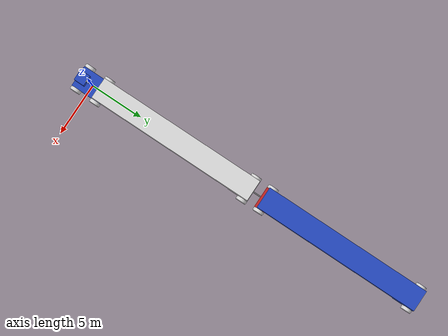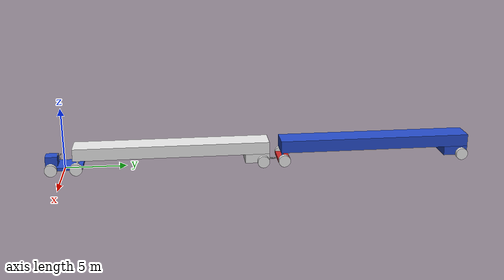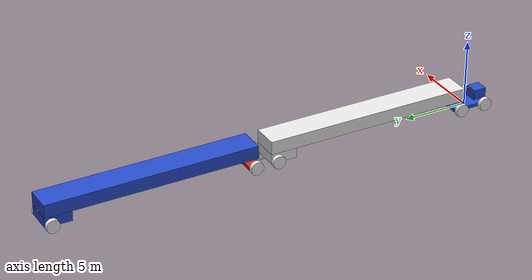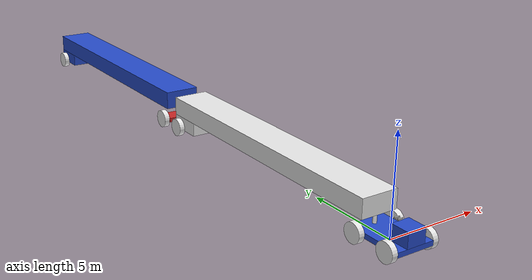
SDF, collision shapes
<?xml version='1.0'?>
<sdf version='1.7'>
  <model name='Double_Trailer_53'>
    <link name='Dolly_Body'>
      <inertial>
        <pose>0 0 0.250023 0 -0 0</pose>
        <mass>2501</mass>
        <inertia>
          <ixx>1909.04</ixx>
          <ixy>0</ixy>
          <ixz>0</ixz>
          <iyy>500.71</iyy>
          <iyz>0</iyz>
          <izz>2541.84</izz>
        </inertia>
      </inertial>
      <self_collide>0</self_collide>
      <enable_wind>0</enable_wind>
      <kinematic>0</kinematic>
      <pose>0 18 0 0 -0 0</pose>
      <gravity>1</gravity>
      <visual name='Dolly_Body_visual'>
        <pose>0 0 0.25 0 -0 0</pose>
        <geometry>
          <box>
            <size>2 1 0.25</size>
          </box>
        </geometry>
        <material>
          <script>
            <name>Gazebo/Red</name>
            <uri>file://media/materials/scripts/gazebo.material</uri>
          </script>
          <shader type='pixel'>
            <normal_map>__default__</normal_map>
          </shader>
          <ambient>1 0 0 1</ambient>
          <diffuse>1 0 0 1</diffuse>
          <specular>0.1 0.1 0.1 1</specular>
          <emissive>0 0 0 1</emissive>
        </material>
        <transparency>0</transparency>
        <cast_shadows>1</cast_shadows>
      </visual>
      <collision name='Dolly_Body_collision'>
        <laser_retro>0</laser_retro>
        <max_contacts>10</max_contacts>
        <pose>0 0 0.25 0 -0 0</pose>
        <geometry>
          <box>
            <size>2 1 0.25</size>
          </box>
        </geometry>
        <surface>
          <friction>
            <ode>
              <mu>1</mu>
              <mu2>1</mu2>
              <fdir1>0 0 0</fdir1>
              <slip1>0</slip1>
              <slip2>0</slip2>
            </ode>
            <torsional>
              <coefficient>1</coefficient>
              <patch_radius>0</patch_radius>
              <surface_radius>0</surface_radius>
              <use_patch_radius>1</use_patch_radius>
              <ode>
                <slip>0</slip>
              </ode>
            </torsional>
          </friction>
          <bounce>
            <restitution_coefficient>0</restitution_coefficient>
            <threshold>1e+06</threshold>
          </bounce>
          <contact>
            <collide_without_contact>0</collide_without_contact>
            <collide_without_contact_bitmask>1</collide_without_contact_bitmask>
            <collide_bitmask>1</collide_bitmask>
            <ode>
              <soft_cfm>0</soft_cfm>
              <soft_erp>0.2</soft_erp>
              <kp>1e+13</kp>
              <kd>1</kd>
              <max_vel>0.01</max_vel>
              <min_depth>0</min_depth>
            </ode>
            <bullet>
              <split_impulse>1</split_impulse>
              <split_impulse_penetration_threshold>-0.01</split_impulse_penetration_threshold>
              <soft_cfm>0</soft_cfm>
              <soft_erp>0.2</soft_erp>
              <kp>1e+13</kp>
              <kd>1</kd>
            </bullet>
          </contact>
        </surface>
      </collision>
    </link>
    <link name='Dolly_driv_wheel'>
      <pose>1.15005 18 0.265 0 -0 0</pose>
      <inertial>
        <pose>0 0 0 0 -0 0</pose>
        <mass>100</mass>
        <inertia>
          <ixx>7</ixx>
          <ixy>0</ixy>
          <ixz>0</ixz>
          <iyy>7</iyy>
          <iyz>0</iyz>
          <izz>12.5</izz>
        </inertia>
      </inertial>
      <self_collide>0</self_collide>
      <enable_wind>0</enable_wind>
      <kinematic>0</kinematic>
      <visual name='Trailer_driv_wheel_visual'>
        <pose>0 0 0 -3.1415 1.57079 3.14159</pose>
        <geometry>
          <cylinder>
            <length>0.3</length>
            <radius>0.5</radius>
          </cylinder>
        </geometry>
        <material>
          <script>
            <name>Gazebo/White</name>
            <uri>file://media/materials/scripts/gazebo.material</uri>
          </script>
          <shader type='pixel'/>
          <emissive>0 0 0 1</emissive>
        </material>
        <transparency>0</transparency>
        <cast_shadows>1</cast_shadows>
      </visual>
      <collision name='Trailer_driv_wheel_collision'>
        <laser_retro>0</laser_retro>
        <max_contacts>10</max_contacts>
        <pose>0 0 0 -3.1415 1.57079 3.14159</pose>
        <geometry>
          <cylinder>
            <radius>0.5</radius>
            <length>0.3</length>
          </cylinder>
        </geometry>
        <surface>
          <friction>
            <ode>
              <mu>1</mu>
              <mu2>1</mu2>
              <fdir1>0 0 0</fdir1>
              <slip1>0</slip1>
              <slip2>0</slip2>
            </ode>
            <torsional>
              <coefficient>1</coefficient>
              <patch_radius>0</patch_radius>
              <surface_radius>0</surface_radius>
              <use_patch_radius>1</use_patch_radius>
              <ode>
                <slip>0</slip>
              </ode>
            </torsional>
          </friction>
          <bounce>
            <restitution_coefficient>0</restitution_coefficient>
            <threshold>1e+06</threshold>
          </bounce>
          <contact>
            <collide_without_contact>0</collide_without_contact>
            <collide_without_contact_bitmask>1</collide_without_contact_bitmask>
            <collide_bitmask>1</collide_bitmask>
            <ode>
              <soft_cfm>0</soft_cfm>
              <soft_erp>0.2</soft_erp>
              <kp>1e+13</kp>
              <kd>1</kd>
              <max_vel>0.01</max_vel>
              <min_depth>0</min_depth>
            </ode>
            <bullet>
              <split_impulse>1</split_impulse>
              <split_impulse_penetration_threshold>-0.01</split_impulse_penetration_threshold>
              <soft_cfm>0</soft_cfm>
              <soft_erp>0.2</soft_erp>
              <kp>1e+13</kp>
              <kd>1</kd>
            </bullet>
          </contact>
        </surface>
      </collision>
    </link>
    <link name='Dolly_pass_wheel'>
      <pose>-1.15005 18 0.265 0 -0 0</pose>
      <inertial>
        <pose>0 0 0 0 -0 0</pose>
        <mass>100</mass>
        <inertia>
          <ixx>7</ixx>
          <ixy>0</ixy>
          <ixz>0</ixz>
          <iyy>7</iyy>
          <iyz>0</iyz>
          <izz>12.5</izz>
        </inertia>
      </inertial>
      <self_collide>0</self_collide>
      <enable_wind>0</enable_wind>
      <kinematic>0</kinematic>
      <visual name='Trailer_pass_wheel_visual'>
        <pose>0 0 0 -3.1415 1.57079 3.14159</pose>
        <geometry>
          <cylinder>
            <length>0.3</length>
            <radius>0.5</radius>
          </cylinder>
        </geometry>
        <material>
          <script>
            <name>Gazebo/White</name>
            <uri>file://media/materials/scripts/gazebo.material</uri>
          </script>
          <shader type='pixel'/>
          <emissive>0 0 0 1</emissive>
        </material>
        <transparency>0</transparency>
        <cast_shadows>1</cast_shadows>
      </visual>
      <collision name='Trailer_pass_wheel_collision'>
        <laser_retro>0</laser_retro>
        <max_contacts>10</max_contacts>
        <pose>0 0 0 -3.1415 1.57079 3.14159</pose>
        <geometry>
          <cylinder>
            <radius>0.5</radius>
            <length>0.3</length>
          </cylinder>
        </geometry>
        <surface>
          <friction>
            <ode>
              <mu>1</mu>
              <mu2>1</mu2>
              <fdir1>0 0 0</fdir1>
              <slip1>0</slip1>
              <slip2>0</slip2>
            </ode>
            <torsional>
              <coefficient>1</coefficient>
              <patch_radius>0</patch_radius>
              <surface_radius>0</surface_radius>
              <use_patch_radius>1</use_patch_radius>
              <ode>
                <slip>0</slip>
              </ode>
            </torsional>
          </friction>
          <bounce>
            <restitution_coefficient>0</restitution_coefficient>
            <threshold>1e+06</threshold>
          </bounce>
          <contact>
            <collide_without_contact>0</collide_without_contact>
            <collide_without_contact_bitmask>1</collide_without_contact_bitmask>
            <collide_bitmask>1</collide_bitmask>
            <ode>
              <soft_cfm>0</soft_cfm>
              <soft_erp>0.2</soft_erp>
              <kp>1e+13</kp>
              <kd>1</kd>
              <max_vel>0.01</max_vel>
              <min_depth>0</min_depth>
            </ode>
            <bullet>
              <split_impulse>1</split_impulse>
              <split_impulse_penetration_threshold>-0.01</split_impulse_penetration_threshold>
              <soft_cfm>0</soft_cfm>
              <soft_erp>0.2</soft_erp>
              <kp>1e+13</kp>
              <kd>1</kd>
            </bullet>
          </contact>
        </surface>
      </collision>
    </link>
    <link name='Front_Axle'>
      <pose>1e-06 -1 0.25 0 -0 0</pose>
      <inertial>
        <pose>0 0 0 0 -0 0</pose>
        <mass>1</mass>
        <inertia>
          <ixx>0</ixx>
          <ixy>0</ixy>
          <ixz>0</ixz>
          <iyy>0</iyy>
          <iyz>0</iyz>
          <izz>0</izz>
        </inertia>
      </inertial>
      <self_collide>0</self_collide>
      <enable_wind>0</enable_wind>
      <kinematic>0</kinematic>
      <visual name='Front_Axle_visual'>
        <pose>0 0 0 -3.1415 1.57079 3.14159</pose>
        <geometry>
          <cylinder>
            <length>2</length>
            <radius>0.1</radius>
          </cylinder>
        </geometry>
        <material>
          <script>
            <name>Gazebo/White</name>
            <uri>file://media/materials/scripts/gazebo.material</uri>
          </script>
          <shader type='pixel'/>
        </material>
        <transparency>0</transparency>
        <cast_shadows>1</cast_shadows>
      </visual>
      <collision name='Front_Axle_collision'>
        <laser_retro>0</laser_retro>
        <max_contacts>10</max_contacts>
        <pose>0 0 0 -3.1415 1.57079 3.14159</pose>
        <geometry>
          <cylinder>
            <radius>0.1</radius>
            <length>2</length>
          </cylinder>
        </geometry>
        <surface>
          <friction>
            <ode>
              <mu>1</mu>
              <mu2>1</mu2>
              <fdir1>0 0 0</fdir1>
              <slip1>0</slip1>
              <slip2>0</slip2>
            </ode>
            <torsional>
              <coefficient>1</coefficient>
              <patch_radius>0</patch_radius>
              <surface_radius>0</surface_radius>
              <use_patch_radius>1</use_patch_radius>
              <ode>
                <slip>0</slip>
              </ode>
            </torsional>
          </friction>
          <bounce>
            <restitution_coefficient>0</restitution_coefficient>
            <threshold>1e+06</threshold>
          </bounce>
          <contact>
            <collide_without_contact>0</collide_without_contact>
            <collide_without_contact_bitmask>1</collide_without_contact_bitmask>
            <collide_bitmask>1</collide_bitmask>
            <ode>
              <soft_cfm>0</soft_cfm>
              <soft_erp>0.2</soft_erp>
              <kp>1e+13</kp>
              <kd>1</kd>
              <max_vel>0.01</max_vel>
              <min_depth>0</min_depth>
            </ode>
            <bullet>
              <split_impulse>1</split_impulse>
              <split_impulse_penetration_threshold>-0.01</split_impulse_penetration_threshold>
              <soft_cfm>0</soft_cfm>
              <soft_erp>0.2</soft_erp>
              <kp>1e+13</kp>
              <kd>1</kd>
            </bullet>
          </contact>
        </surface>
      </collision>
    </link>
    <link name='Tractor_Body'>
      <inertial>
        <pose>0 0 0.250023 0 -0 0</pose>
        <mass>6501</mass>
        <inertia>
          <ixx>4909.04</ixx>
          <ixy>0</ixy>
          <ixz>0</ixz>
          <iyy>2200.71</iyy>
          <iyz>0</iyz>
          <izz>7041.84</izz>
        </inertia>
      </inertial>
      <self_collide>0</self_collide>
      <enable_wind>0</enable_wind>
      <kinematic>0</kinematic>
      <pose>0 0 0 0 -0 0</pose>
      <gravity>1</gravity>
      <visual name='Tractor_Body_fixed_joint_lump__Tractor_Weighted_Base_visual_1'>
        <pose>0 0 0.25 0 -0 0</pose>
        <geometry>
          <box>
            <size>2 3 0.25</size>
          </box>
        </geometry>
        <material>
          <script>
            <name>Gazebo/Blue</name>
            <uri>file://media/materials/scripts/gazebo.material</uri>
          </script>
          <shader type='pixel'>
            <normal_map>__default__</normal_map>
          </shader>
        </material>
        <transparency>0</transparency>
        <cast_shadows>1</cast_shadows>
      </visual>
      <visual name='Tractor_Body_visual'>
        <pose>0 0 0.25 0 -0 0</pose>
        <geometry>
          <box>
            <size>2 3 0.25</size>
          </box>
        </geometry>
        <material>
          <script>
            <name>Gazebo/Blue</name>
            <uri>file://media/materials/scripts/gazebo.material</uri>
          </script>
          <shader type='pixel'>
            <normal_map>__default__</normal_map>
          </shader>
        </material>
        <transparency>0</transparency>
        <cast_shadows>1</cast_shadows>
      </visual>
      <visual name='Tractor_Body_fixed_joint_lump__Tractor_Cab_visual_2'>
        <pose>0 -1 0.65 0 -0 0</pose>
        <geometry>
          <box>
            <size>1 1 1</size>
          </box>
        </geometry>
        <material>
          <script>
            <name>Gazebo/Blue</name>
            <uri>file://media/materials/scripts/gazebo.material</uri>
          </script>
          <shader type='pixel'>
            <normal_map>__default__</normal_map>
          </shader>
        </material>
        <transparency>0</transparency>
        <cast_shadows>1</cast_shadows>
      </visual>
      <collision name='Tractor_Body_fixed_joint_lump__Tractor_Cab_collision_2'>
        <laser_retro>0</laser_retro>
        <max_contacts>10</max_contacts>
        <pose>0 -1 0.65 0 -0 0</pose>
        <geometry>
          <box>
            <size>1 1 1</size>
          </box>
        </geometry>
        <surface>
          <friction>
            <ode>
              <mu>1</mu>
              <mu2>1</mu2>
              <fdir1>0 0 0</fdir1>
              <slip1>0</slip1>
              <slip2>0</slip2>
            </ode>
            <torsional>
              <coefficient>1</coefficient>
              <patch_radius>0</patch_radius>
              <surface_radius>0</surface_radius>
              <use_patch_radius>1</use_patch_radius>
              <ode>
                <slip>0</slip>
              </ode>
            </torsional>
          </friction>
          <bounce>
            <restitution_coefficient>0</restitution_coefficient>
            <threshold>1e+06</threshold>
          </bounce>
          <contact>
            <collide_without_contact>0</collide_without_contact>
            <collide_without_contact_bitmask>1</collide_without_contact_bitmask>
            <collide_bitmask>1</collide_bitmask>
            <ode>
              <soft_cfm>0</soft_cfm>
              <soft_erp>0.2</soft_erp>
              <kp>1e+13</kp>
              <kd>1</kd>
              <max_vel>0.01</max_vel>
              <min_depth>0</min_depth>
            </ode>
            <bullet>
              <split_impulse>1</split_impulse>
              <split_impulse_penetration_threshold>-0.01</split_impulse_penetration_threshold>
              <soft_cfm>0</soft_cfm>
              <soft_erp>0.2</soft_erp>
              <kp>1e+13</kp>
              <kd>1</kd>
            </bullet>
          </contact>
        </surface>
      </collision>
      <collision name='Tractor_Body_collision'>
        <laser_retro>0</laser_retro>
        <max_contacts>10</max_contacts>
        <pose>0 0 0.25 0 -0 0</pose>
        <geometry>
          <box>
            <size>2 3 0.25</size>
          </box>
        </geometry>
        <surface>
          <friction>
            <ode>
              <mu>1</mu>
              <mu2>1</mu2>
              <fdir1>0 0 0</fdir1>
              <slip1>0</slip1>
              <slip2>0</slip2>
            </ode>
            <torsional>
              <coefficient>1</coefficient>
              <patch_radius>0</patch_radius>
              <surface_radius>0</surface_radius>
              <use_patch_radius>1</use_patch_radius>
              <ode>
                <slip>0</slip>
              </ode>
            </torsional>
          </friction>
          <bounce>
            <restitution_coefficient>0</restitution_coefficient>
            <threshold>1e+06</threshold>
          </bounce>
          <contact>
            <collide_without_contact>0</collide_without_contact>
            <collide_without_contact_bitmask>1</collide_without_contact_bitmask>
            <collide_bitmask>1</collide_bitmask>
            <ode>
              <soft_cfm>0</soft_cfm>
              <soft_erp>0.2</soft_erp>
              <kp>1e+13</kp>
              <kd>1</kd>
              <max_vel>0.01</max_vel>
              <min_depth>0</min_depth>
            </ode>
            <bullet>
              <split_impulse>1</split_impulse>
              <split_impulse_penetration_threshold>-0.01</split_impulse_penetration_threshold>
              <soft_cfm>0</soft_cfm>
              <soft_erp>0.2</soft_erp>
              <kp>1e+13</kp>
              <kd>1</kd>
            </bullet>
          </contact>
        </surface>
      </collision>
      <collision name='Tractor_Body_fixed_joint_lump__Tractor_Weighted_Base_collision_1'>
        <laser_retro>0</laser_retro>
        <max_contacts>10</max_contacts>
        <pose>0 0 0.25 0 -0 0</pose>
        <geometry>
          <box>
            <size>2 3 0.25</size>
          </box>
        </geometry>
        <surface>
          <friction>
            <ode>
              <mu>1</mu>
              <mu2>1</mu2>
              <fdir1>0 0 0</fdir1>
              <slip1>0</slip1>
              <slip2>0</slip2>
            </ode>
            <torsional>
              <coefficient>1</coefficient>
              <patch_radius>0</patch_radius>
              <surface_radius>0</surface_radius>
              <use_patch_radius>1</use_patch_radius>
              <ode>
                <slip>0</slip>
              </ode>
            </torsional>
          </friction>
          <bounce>
            <restitution_coefficient>0</restitution_coefficient>
            <threshold>1e+06</threshold>
          </bounce>
          <contact>
            <collide_without_contact>0</collide_without_contact>
            <collide_without_contact_bitmask>1</collide_without_contact_bitmask>
            <collide_bitmask>1</collide_bitmask>
            <ode>
              <soft_cfm>0</soft_cfm>
              <soft_erp>0.2</soft_erp>
              <kp>1e+13</kp>
              <kd>1</kd>
              <max_vel>0.01</max_vel>
              <min_depth>0</min_depth>
            </ode>
            <bullet>
              <split_impulse>1</split_impulse>
              <split_impulse_penetration_threshold>-0.01</split_impulse_penetration_threshold>
              <soft_cfm>0</soft_cfm>
              <soft_erp>0.2</soft_erp>
              <kp>1e+13</kp>
              <kd>1</kd>
            </bullet>
          </contact>
        </surface>
      </collision>
    </link>
    <link name='Tractor_front_driv_wheel'>
      <pose>1.15 -0.999999 0.25 0 -0 0</pose>
      <inertial>
        <pose>0 0 0 0 -0 0</pose>
        <mass>50</mass>
        <inertia>
          <ixx>2.45</ixx>
          <ixy>0</ixy>
          <ixz>0</ixz>
          <iyy>2.45</iyy>
          <iyz>0</iyz>
          <izz>4.375</izz>
        </inertia>
      </inertial>
      <self_collide>0</self_collide>
      <enable_wind>0</enable_wind>
      <kinematic>0</kinematic>
      <visual name='Tractor_front_driv_wheel_visual'>
        <pose>0 0 0 -3.1415 1.57079 3.14159</pose>
        <geometry>
          <cylinder>
            <length>0.3</length>
            <radius>0.5</radius>
          </cylinder>
        </geometry>
        <material>
          <script>
            <name>Gazebo/White</name>
            <uri>file://media/materials/scripts/gazebo.material</uri>
          </script>
          <shader type='pixel'/>
        </material>
        <transparency>0</transparency>
        <cast_shadows>1</cast_shadows>
      </visual>
      <collision name='Tractor_front_driv_wheel_collision'>
        <laser_retro>0</laser_retro>
        <max_contacts>10</max_contacts>
        <pose>0 0 0 -3.1415 1.57079 3.14159</pose>
        <geometry>
          <cylinder>
            <radius>0.5</radius>
            <length>0.3</length>
          </cylinder>
        </geometry>
        <surface>
          <friction>
            <ode>
              <mu>1</mu>
              <mu2>1</mu2>
              <fdir1>0 0 0</fdir1>
              <slip1>0</slip1>
              <slip2>0</slip2>
            </ode>
            <torsional>
              <coefficient>1</coefficient>
              <patch_radius>0</patch_radius>
              <surface_radius>0</surface_radius>
              <use_patch_radius>1</use_patch_radius>
              <ode>
                <slip>0</slip>
              </ode>
            </torsional>
          </friction>
          <bounce>
            <restitution_coefficient>0</restitution_coefficient>
            <threshold>1e+06</threshold>
          </bounce>
          <contact>
            <collide_without_contact>0</collide_without_contact>
            <collide_without_contact_bitmask>1</collide_without_contact_bitmask>
            <collide_bitmask>1</collide_bitmask>
            <ode>
              <soft_cfm>0</soft_cfm>
              <soft_erp>0.2</soft_erp>
              <kp>1e+13</kp>
              <kd>1</kd>
              <max_vel>0.01</max_vel>
              <min_depth>0</min_depth>
            </ode>
            <bullet>
              <split_impulse>1</split_impulse>
              <split_impulse_penetration_threshold>-0.01</split_impulse_penetration_threshold>
              <soft_cfm>0</soft_cfm>
              <soft_erp>0.2</soft_erp>
              <kp>1e+13</kp>
              <kd>1</kd>
            </bullet>
          </contact>
        </surface>
      </collision>
    </link>
    <link name='Tractor_front_pass_wheel'>
      <pose>-1.15 -1 0.25 0 -0 0</pose>
      <inertial>
        <pose>0 0 0 0 -0 0</pose>
        <mass>50</mass>
        <inertia>
          <ixx>3.5</ixx>
          <ixy>0</ixy>
          <ixz>0</ixz>
          <iyy>3.5</iyy>
          <iyz>0</iyz>
          <izz>6.25</izz>
        </inertia>
      </inertial>
      <self_collide>0</self_collide>
      <enable_wind>0</enable_wind>
      <kinematic>0</kinematic>
      <visual name='Tractor_front_pass_wheel_visual'>
        <pose>0 0 0 -3.1415 1.57079 3.14159</pose>
        <geometry>
          <cylinder>
            <length>0.3</length>
            <radius>0.5</radius>
          </cylinder>
        </geometry>
        <material>
          <script>
            <name>Gazebo/White</name>
            <uri>file://media/materials/scripts/gazebo.material</uri>
          </script>
          <shader type='pixel'/>
        </material>
        <transparency>0</transparency>
        <cast_shadows>1</cast_shadows>
      </visual>
      <collision name='Tractor_front_pass_wheel_collision'>
        <laser_retro>0</laser_retro>
        <max_contacts>10</max_contacts>
        <pose>0 0 0 -3.1415 1.57079 3.14159</pose>
        <geometry>
          <cylinder>
            <radius>0.5</radius>
            <length>0.3</length>
          </cylinder>
        </geometry>
        <surface>
          <friction>
            <ode>
              <mu>1</mu>
              <mu2>1</mu2>
              <fdir1>0 0 0</fdir1>
              <slip1>0</slip1>
              <slip2>0</slip2>
            </ode>
            <torsional>
              <coefficient>1</coefficient>
              <patch_radius>0</patch_radius>
              <surface_radius>0</surface_radius>
              <use_patch_radius>1</use_patch_radius>
              <ode>
                <slip>0</slip>
              </ode>
            </torsional>
          </friction>
          <bounce>
            <restitution_coefficient>0</restitution_coefficient>
            <threshold>1e+06</threshold>
          </bounce>
          <contact>
            <collide_without_contact>0</collide_without_contact>
            <collide_without_contact_bitmask>1</collide_without_contact_bitmask>
            <collide_bitmask>1</collide_bitmask>
            <ode>
              <soft_cfm>0</soft_cfm>
              <soft_erp>0.2</soft_erp>
              <kp>1e+13</kp>
              <kd>1</kd>
              <max_vel>0.01</max_vel>
              <min_depth>0</min_depth>
            </ode>
            <bullet>
              <split_impulse>1</split_impulse>
              <split_impulse_penetration_threshold>-0.01</split_impulse_penetration_threshold>
              <soft_cfm>0</soft_cfm>
              <soft_erp>0.2</soft_erp>
              <kp>1e+13</kp>
              <kd>1</kd>
            </bullet>
          </contact>
        </surface>
      </collision>
    </link>
    <link name='Tractor_rear_driv_wheel'>
      <pose>1.15 1 0.2525 0 -0 0</pose>
      <inertial>
        <pose>0 0 0 0 -0 0</pose>
        <mass>100</mass>
        <inertia>
          <ixx>7</ixx>
          <ixy>0</ixy>
          <ixz>0</ixz>
          <iyy>7</iyy>
          <iyz>0</iyz>
          <izz>12.5</izz>
        </inertia>
      </inertial>
      <self_collide>0</self_collide>
      <enable_wind>0</enable_wind>
      <kinematic>0</kinematic>
      <visual name='Tractor_rear_driv_wheel_visual'>
        <pose>0 0 0 -3.1415 1.57079 3.14159</pose>
        <geometry>
          <cylinder>
            <length>0.3</length>
            <radius>0.5</radius>
          </cylinder>
        </geometry>
        <material>
          <script>
            <name>Gazebo/White</name>
            <uri>file://media/materials/scripts/gazebo.material</uri>
          </script>
          <shader type='pixel'/>
        </material>
        <transparency>0</transparency>
        <cast_shadows>1</cast_shadows>
      </visual>
      <collision name='Tractor_rear_driv_wheel_collision'>
        <laser_retro>0</laser_retro>
        <max_contacts>10</max_contacts>
        <pose>0 0 0 -3.1415 1.57079 3.14159</pose>
        <geometry>
          <cylinder>
            <radius>0.5</radius>
            <length>0.3</length>
          </cylinder>
        </geometry>
        <surface>
          <friction>
            <ode>
              <mu>1</mu>
              <mu2>1</mu2>
              <fdir1>0 0 0</fdir1>
              <slip1>0</slip1>
              <slip2>0</slip2>
            </ode>
            <torsional>
              <coefficient>1</coefficient>
              <patch_radius>0</patch_radius>
              <surface_radius>0</surface_radius>
              <use_patch_radius>1</use_patch_radius>
              <ode>
                <slip>0</slip>
              </ode>
            </torsional>
          </friction>
          <bounce>
            <restitution_coefficient>0</restitution_coefficient>
            <threshold>1e+06</threshold>
          </bounce>
          <contact>
            <collide_without_contact>0</collide_without_contact>
            <collide_without_contact_bitmask>1</collide_without_contact_bitmask>
            <collide_bitmask>1</collide_bitmask>
            <ode>
              <soft_cfm>0</soft_cfm>
              <soft_erp>0.2</soft_erp>
              <kp>1e+13</kp>
              <kd>1</kd>
              <max_vel>0.01</max_vel>
              <min_depth>0</min_depth>
            </ode>
            <bullet>
              <split_impulse>1</split_impulse>
              <split_impulse_penetration_threshold>-0.01</split_impulse_penetration_threshold>
              <soft_cfm>0</soft_cfm>
              <soft_erp>0.2</soft_erp>
              <kp>1e+13</kp>
              <kd>1</kd>
            </bullet>
          </contact>
        </surface>
      </collision>
    </link>
    <link name='Tractor_rear_pass_wheel'>
      <pose>-1.15 0.999999 0.2525 0 -0 0</pose>
      <inertial>
        <pose>0 0 0 0 -0 0</pose>
        <mass>100</mass>
        <inertia>
          <ixx>7</ixx>
          <ixy>0</ixy>
          <ixz>0</ixz>
          <iyy>7</iyy>
          <iyz>0</iyz>
          <izz>12.5</izz>
        </inertia>
      </inertial>
      <self_collide>0</self_collide>
      <enable_wind>0</enable_wind>
      <kinematic>0</kinematic>
      <visual name='Tractor_rear_pass_wheel_visual'>
        <pose>0 0 0 -3.1415 1.57079 3.14159</pose>
        <geometry>
          <cylinder>
            <length>0.3</length>
            <radius>0.5</radius>
          </cylinder>
        </geometry>
        <material>
          <script>
            <name>Gazebo/White</name>
            <uri>file://media/materials/scripts/gazebo.material</uri>
          </script>
          <shader type='pixel'/>
        </material>
        <transparency>0</transparency>
        <cast_shadows>1</cast_shadows>
      </visual>
      <collision name='Tractor_rear_pass_wheel_collision'>
        <laser_retro>0</laser_retro>
        <max_contacts>10</max_contacts>
        <pose>0 0 0 -3.1415 1.57079 3.14159</pose>
        <geometry>
          <cylinder>
            <radius>0.5</radius>
            <length>0.3</length>
          </cylinder>
        </geometry>
        <surface>
          <friction>
            <ode>
              <mu>1</mu>
              <mu2>1</mu2>
              <fdir1>0 0 0</fdir1>
              <slip1>0</slip1>
              <slip2>0</slip2>
            </ode>
            <torsional>
              <coefficient>1</coefficient>
              <patch_radius>0</patch_radius>
              <surface_radius>0</surface_radius>
              <use_patch_radius>1</use_patch_radius>
              <ode>
                <slip>0</slip>
              </ode>
            </torsional>
          </friction>
          <bounce>
            <restitution_coefficient>0</restitution_coefficient>
            <threshold>1e+06</threshold>
          </bounce>
          <contact>
            <collide_without_contact>0</collide_without_contact>
            <collide_without_contact_bitmask>1</collide_without_contact_bitmask>
            <collide_bitmask>1</collide_bitmask>
            <ode>
              <soft_cfm>0</soft_cfm>
              <soft_erp>0.2</soft_erp>
              <kp>1e+13</kp>
              <kd>1</kd>
              <max_vel>0.01</max_vel>
              <min_depth>0</min_depth>
            </ode>
            <bullet>
              <split_impulse>1</split_impulse>
              <split_impulse_penetration_threshold>-0.01</split_impulse_penetration_threshold>
              <soft_cfm>0</soft_cfm>
              <soft_erp>0.2</soft_erp>
              <kp>1e+13</kp>
              <kd>1</kd>
            </bullet>
          </contact>
        </surface>
      </collision>
    </link>
    <link name='Trailer_Hitch'>
      <pose>0 0.999999 0.64 0 -0 0</pose>
      <inertial>
        <pose>0 7.74995 0.749892 0 -0 0</pose>
        <mass>15002</mass>
        <inertia>
          <ixx>321361</ixx>
          <ixy>0</ixy>
          <ixz>0</ixz>
          <iyy>6251.64</iyy>
          <iyz>0.312581</iyz>
          <izz>325109</izz>
        </inertia>
      </inertial>
      <self_collide>0</self_collide>
      <enable_wind>0</enable_wind>
      <kinematic>0</kinematic>
      <visual name='Trailer_Hitch_fixed_joint_lump__Trailer_Body_visual_1'>
        <pose>0 7.75 0.75 0 -0 0</pose>
        <geometry>
          <box>
            <size>2 16 1</size>
          </box>
        </geometry>
        <material>
          <script>
            <name>Gazebo/White</name>
            <uri>file://media/materials/scripts/gazebo.material</uri>
          </script>
          <shader type='pixel'/>
          <emissive>0 0 0 1</emissive>
        </material>
        <transparency>0</transparency>
        <cast_shadows>1</cast_shadows>
      </visual>
      <visual name='Trailer_Hitch_fixed_joint_lump__Trailer_Bottom_visual_2'>
        <pose>0 14.75 -0.125 0 -0 0</pose>
        <geometry>
          <box>
            <size>2 2 0.75</size>
          </box>
        </geometry>
        <material>
          <script>
            <name>Gazebo/Blue</name>
            <uri>file://media/materials/scripts/gazebo.material</uri>
          </script>
          <shader type='pixel'/>
          <emissive>0 0 0 1</emissive>
        </material>
        <transparency>0</transparency>
        <cast_shadows>1</cast_shadows>
      </visual>
      <visual name='Trailer_Hitch_visual'>
        <pose>0 0 0 0 -0 0</pose>
        <geometry>
          <cylinder>
            <length>0.5</length>
            <radius>0.1</radius>
          </cylinder>
        </geometry>
        <material>
          <script>
            <name>Gazebo/White</name>
            <uri>file://media/materials/scripts/gazebo.material</uri>
          </script>
          <shader type='pixel'/>
          <emissive>0 0 0 1</emissive>
        </material>
        <transparency>0</transparency>
        <cast_shadows>1</cast_shadows>
      </visual>
      <collision name='Trailer_Hitch_fixed_joint_lump__Trailer_Bottom_collision_2'>
        <laser_retro>0</laser_retro>
        <max_contacts>10</max_contacts>
        <pose>0 14.75 -0.125 0 -0 0</pose>
        <geometry>
          <box>
            <size>2 2 0.75</size>
          </box>
        </geometry>
        <surface>
          <friction>
            <ode>
              <mu>1</mu>
              <mu2>1</mu2>
              <fdir1>0 0 0</fdir1>
              <slip1>0</slip1>
              <slip2>0</slip2>
            </ode>
            <torsional>
              <coefficient>1</coefficient>
              <patch_radius>0</patch_radius>
              <surface_radius>0</surface_radius>
              <use_patch_radius>1</use_patch_radius>
              <ode>
                <slip>0</slip>
              </ode>
            </torsional>
          </friction>
          <bounce>
            <restitution_coefficient>0</restitution_coefficient>
            <threshold>1e+06</threshold>
          </bounce>
          <contact>
            <collide_without_contact>0</collide_without_contact>
            <collide_without_contact_bitmask>1</collide_without_contact_bitmask>
            <collide_bitmask>1</collide_bitmask>
            <ode>
              <soft_cfm>0</soft_cfm>
              <soft_erp>0.2</soft_erp>
              <kp>1e+13</kp>
              <kd>1</kd>
              <max_vel>0.01</max_vel>
              <min_depth>0</min_depth>
            </ode>
            <bullet>
              <split_impulse>1</split_impulse>
              <split_impulse_penetration_threshold>-0.01</split_impulse_penetration_threshold>
              <soft_cfm>0</soft_cfm>
              <soft_erp>0.2</soft_erp>
              <kp>1e+13</kp>
              <kd>1</kd>
            </bullet>
          </contact>
        </surface>
      </collision>
      <collision name='Trailer_Hitch_fixed_joint_lump__Trailer_Body_collision_1'>
        <laser_retro>0</laser_retro>
        <max_contacts>10</max_contacts>
        <pose>0 7.75 0.75 0 -0 0</pose>
        <geometry>
          <box>
            <size>2 16 1</size>
          </box>
        </geometry>
        <surface>
          <friction>
            <ode>
              <mu>1</mu>
              <mu2>1</mu2>
              <fdir1>0 0 0</fdir1>
              <slip1>0</slip1>
              <slip2>0</slip2>
            </ode>
            <torsional>
              <coefficient>1</coefficient>
              <patch_radius>0</patch_radius>
              <surface_radius>0</surface_radius>
              <use_patch_radius>1</use_patch_radius>
              <ode>
                <slip>0</slip>
              </ode>
            </torsional>
          </friction>
          <bounce>
            <restitution_coefficient>0</restitution_coefficient>
            <threshold>1e+06</threshold>
          </bounce>
          <contact>
            <collide_without_contact>0</collide_without_contact>
            <collide_without_contact_bitmask>1</collide_without_contact_bitmask>
            <collide_bitmask>1</collide_bitmask>
            <ode>
              <soft_cfm>0</soft_cfm>
              <soft_erp>0.2</soft_erp>
              <kp>1e+13</kp>
              <kd>1</kd>
              <max_vel>0.01</max_vel>
              <min_depth>0</min_depth>
            </ode>
            <bullet>
              <split_impulse>1</split_impulse>
              <split_impulse_penetration_threshold>-0.01</split_impulse_penetration_threshold>
              <soft_cfm>0</soft_cfm>
              <soft_erp>0.2</soft_erp>
              <kp>1e+13</kp>
              <kd>1</kd>
            </bullet>
          </contact>
        </surface>
      </collision>
      <collision name='Trailer_Hitch_collision'>
        <laser_retro>0</laser_retro>
        <max_contacts>10</max_contacts>
        <pose>0 0 0 0 -0 0</pose>
        <geometry>
          <cylinder>
            <radius>0.1</radius>
            <length>0.5</length>
          </cylinder>
        </geometry>
        <surface>
          <friction>
            <ode>
              <mu>1</mu>
              <mu2>1</mu2>
              <fdir1>0 0 0</fdir1>
              <slip1>0</slip1>
              <slip2>0</slip2>
            </ode>
            <torsional>
              <coefficient>1</coefficient>
              <patch_radius>0</patch_radius>
              <surface_radius>0</surface_radius>
              <use_patch_radius>1</use_patch_radius>
              <ode>
                <slip>0</slip>
              </ode>
            </torsional>
          </friction>
          <bounce>
            <restitution_coefficient>0</restitution_coefficient>
            <threshold>1e+06</threshold>
          </bounce>
          <contact>
            <collide_without_contact>0</collide_without_contact>
            <collide_without_contact_bitmask>1</collide_without_contact_bitmask>
            <collide_bitmask>1</collide_bitmask>
            <ode>
              <soft_cfm>0</soft_cfm>
              <soft_erp>0.2</soft_erp>
              <kp>1e+13</kp>
              <kd>1</kd>
              <max_vel>0.01</max_vel>
              <min_depth>0</min_depth>
            </ode>
            <bullet>
              <split_impulse>1</split_impulse>
              <split_impulse_penetration_threshold>-0.01</split_impulse_penetration_threshold>
              <soft_cfm>0</soft_cfm>
              <soft_erp>0.2</soft_erp>
              <kp>1e+13</kp>
              <kd>1</kd>
            </bullet>
          </contact>
        </surface>
      </collision>
    </link>
    <link name='second_trailer'>
      <pose>0 18 0.64 0 -0 0</pose>
      <inertial>
        <pose>0 7.74995 0.749892 0 -0 0</pose>
        <mass>15002</mass>
        <inertia>
          <ixx>321361</ixx>
          <ixy>0</ixy>
          <ixz>0</ixz>
          <iyy>6251.64</iyy>
          <iyz>0.312581</iyz>
          <izz>325109</izz>
        </inertia>
      </inertial>
      <self_collide>0</self_collide>
      <enable_wind>0</enable_wind>
      <kinematic>0</kinematic>
      <visual name='Trailer_Hitch_fixed_joint_lump__Trailer_Bottom_visual_2'>
        <pose>0 14.75 -0.125 0 -0 0</pose>
        <geometry>
          <box>
            <size>2 2 0.75</size>
          </box>
        </geometry>
        <material>
          <script>
            <name>Gazebo/Blue</name>
            <uri>file://media/materials/scripts/gazebo.material</uri>
          </script>
          <shader type='pixel'/>
          <emissive>0 0 0 1</emissive>
        </material>
        <transparency>0</transparency>
        <cast_shadows>1</cast_shadows>
      </visual>
      <visual name='Trailer_Hitch_fixed_joint_lump__Trailer_Body_visual_1'>
        <pose>0 7.75 0.75 0 -0 0</pose>
        <geometry>
          <box>
            <size>2 16 1</size>
          </box>
        </geometry>
        <material>
          <script>
            <name>Gazebo/White</name>
            <uri>file://media/materials/scripts/gazebo.material</uri>
          </script>
          <shader type='pixel'/>
          <emissive>0 0 0 1</emissive>
        </material>
        <transparency>0</transparency>
        <cast_shadows>1</cast_shadows>
      </visual>
      <visual name='Trailer_Hitch_visual'>
        <pose>0 0 0 0 -0 0</pose>
        <geometry>
          <cylinder>
            <length>0.5</length>
            <radius>0.1</radius>
          </cylinder>
        </geometry>
        <material>
          <script>
            <name>Gazebo/White</name>
            <uri>file://media/materials/scripts/gazebo.material</uri>
          </script>
          <shader type='pixel'/>
          <emissive>0 0 0 1</emissive>
        </material>
        <transparency>0</transparency>
        <cast_shadows>1</cast_shadows>
      </visual>
      <collision name='Trailer_Hitch_collision'>
        <laser_retro>0</laser_retro>
        <max_contacts>10</max_contacts>
        <pose>0 0 0 0 -0 0</pose>
        <geometry>
          <cylinder>
            <radius>0.1</radius>
            <length>0.5</length>
          </cylinder>
        </geometry>
        <surface>
          <friction>
            <ode>
              <mu>1</mu>
              <mu2>1</mu2>
              <fdir1>0 0 0</fdir1>
              <slip1>0</slip1>
              <slip2>0</slip2>
            </ode>
            <torsional>
              <coefficient>1</coefficient>
              <patch_radius>0</patch_radius>
              <surface_radius>0</surface_radius>
              <use_patch_radius>1</use_patch_radius>
              <ode>
                <slip>0</slip>
              </ode>
            </torsional>
          </friction>
          <bounce>
            <restitution_coefficient>0</restitution_coefficient>
            <threshold>1e+06</threshold>
          </bounce>
          <contact>
            <collide_without_contact>0</collide_without_contact>
            <collide_without_contact_bitmask>1</collide_without_contact_bitmask>
            <collide_bitmask>1</collide_bitmask>
            <ode>
              <soft_cfm>0</soft_cfm>
              <soft_erp>0.2</soft_erp>
              <kp>1e+13</kp>
              <kd>1</kd>
              <max_vel>0.01</max_vel>
              <min_depth>0</min_depth>
            </ode>
            <bullet>
              <split_impulse>1</split_impulse>
              <split_impulse_penetration_threshold>-0.01</split_impulse_penetration_threshold>
              <soft_cfm>0</soft_cfm>
              <soft_erp>0.2</soft_erp>
              <kp>1e+13</kp>
              <kd>1</kd>
            </bullet>
          </contact>
        </surface>
      </collision>
      <collision name='Trailer_Hitch_fixed_joint_lump__Trailer_Body_collision_1'>
        <laser_retro>0</laser_retro>
        <max_contacts>10</max_contacts>
        <pose>0 7.75 0.75 0 -0 0</pose>
        <geometry>
          <box>
            <size>2 16 1</size>
          </box>
        </geometry>
        <surface>
          <friction>
            <ode>
              <mu>1</mu>
              <mu2>1</mu2>
              <fdir1>0 0 0</fdir1>
              <slip1>0</slip1>
              <slip2>0</slip2>
            </ode>
            <torsional>
              <coefficient>1</coefficient>
              <patch_radius>0</patch_radius>
              <surface_radius>0</surface_radius>
              <use_patch_radius>1</use_patch_radius>
              <ode>
                <slip>0</slip>
              </ode>
            </torsional>
          </friction>
          <bounce>
            <restitution_coefficient>0</restitution_coefficient>
            <threshold>1e+06</threshold>
          </bounce>
          <contact>
            <collide_without_contact>0</collide_without_contact>
            <collide_without_contact_bitmask>1</collide_without_contact_bitmask>
            <collide_bitmask>1</collide_bitmask>
            <ode>
              <soft_cfm>0</soft_cfm>
              <soft_erp>0.2</soft_erp>
              <kp>1e+13</kp>
              <kd>1</kd>
              <max_vel>0.01</max_vel>
              <min_depth>0</min_depth>
            </ode>
            <bullet>
              <split_impulse>1</split_impulse>
              <split_impulse_penetration_threshold>-0.01</split_impulse_penetration_threshold>
              <soft_cfm>0</soft_cfm>
              <soft_erp>0.2</soft_erp>
              <kp>1e+13</kp>
              <kd>1</kd>
            </bullet>
          </contact>
        </surface>
      </collision>
      <collision name='Trailer_Hitch_fixed_joint_lump__Trailer_Bottom_collision_2'>
        <laser_retro>0</laser_retro>
        <max_contacts>10</max_contacts>
        <pose>0 14.75 -0.125 0 -0 0</pose>
        <geometry>
          <box>
            <size>2 2 0.75</size>
          </box>
        </geometry>
        <surface>
          <friction>
            <ode>
              <mu>1</mu>
              <mu2>1</mu2>
              <fdir1>0 0 0</fdir1>
              <slip1>0</slip1>
              <slip2>0</slip2>
            </ode>
            <torsional>
              <coefficient>1</coefficient>
              <patch_radius>0</patch_radius>
              <surface_radius>0</surface_radius>
              <use_patch_radius>1</use_patch_radius>
              <ode>
                <slip>0</slip>
              </ode>
            </torsional>
          </friction>
          <bounce>
            <restitution_coefficient>0</restitution_coefficient>
            <threshold>1e+06</threshold>
          </bounce>
          <contact>
            <collide_without_contact>0</collide_without_contact>
            <collide_without_contact_bitmask>1</collide_without_contact_bitmask>
            <collide_bitmask>1</collide_bitmask>
            <ode>
              <soft_cfm>0</soft_cfm>
              <soft_erp>0.2</soft_erp>
              <kp>1e+13</kp>
              <kd>1</kd>
              <max_vel>0.01</max_vel>
              <min_depth>0</min_depth>
            </ode>
            <bullet>
              <split_impulse>1</split_impulse>
              <split_impulse_penetration_threshold>-0.01</split_impulse_penetration_threshold>
              <soft_cfm>0</soft_cfm>
              <soft_erp>0.2</soft_erp>
              <kp>1e+13</kp>
              <kd>1</kd>
            </bullet>
          </contact>
        </surface>
      </collision>
    </link>
    <link name='Trailer_driv_wheel'>
      <pose>1.15 16.25 0.265 0 -0 0</pose>
      <inertial>
        <pose>0 0 0 0 -0 0</pose>
        <mass>100</mass>
        <inertia>
          <ixx>7</ixx>
          <ixy>0</ixy>
          <ixz>0</ixz>
          <iyy>7</iyy>
          <iyz>0</iyz>
          <izz>12.5</izz>
        </inertia>
      </inertial>
      <self_collide>0</self_collide>
      <enable_wind>0</enable_wind>
      <kinematic>0</kinematic>
      <visual name='Trailer_driv_wheel_visual'>
        <pose>0 0 0 -3.1415 1.57079 3.14159</pose>
        <geometry>
          <cylinder>
            <length>0.3</length>
            <radius>0.5</radius>
          </cylinder>
        </geometry>
        <material>
          <script>
            <name>Gazebo/White</name>
            <uri>file://media/materials/scripts/gazebo.material</uri>
          </script>
          <shader type='pixel'/>
          <emissive>0 0 0 1</emissive>
        </material>
        <transparency>0</transparency>
        <cast_shadows>1</cast_shadows>
      </visual>
      <collision name='Trailer_driv_wheel_collision'>
        <laser_retro>0</laser_retro>
        <max_contacts>10</max_contacts>
        <pose>0 0 0 -3.1415 1.57079 3.14159</pose>
        <geometry>
          <cylinder>
            <radius>0.5</radius>
            <length>0.3</length>
          </cylinder>
        </geometry>
        <surface>
          <friction>
            <ode>
              <mu>1</mu>
              <mu2>1</mu2>
              <fdir1>0 0 0</fdir1>
              <slip1>0</slip1>
              <slip2>0</slip2>
            </ode>
            <torsional>
              <coefficient>1</coefficient>
              <patch_radius>0</patch_radius>
              <surface_radius>0</surface_radius>
              <use_patch_radius>1</use_patch_radius>
              <ode>
                <slip>0</slip>
              </ode>
            </torsional>
          </friction>
          <bounce>
            <restitution_coefficient>0</restitution_coefficient>
            <threshold>1e+06</threshold>
          </bounce>
          <contact>
            <collide_without_contact>0</collide_without_contact>
            <collide_without_contact_bitmask>1</collide_without_contact_bitmask>
            <collide_bitmask>1</collide_bitmask>
            <ode>
              <soft_cfm>0</soft_cfm>
              <soft_erp>0.2</soft_erp>
              <kp>1e+13</kp>
              <kd>1</kd>
              <max_vel>0.01</max_vel>
              <min_depth>0</min_depth>
            </ode>
            <bullet>
              <split_impulse>1</split_impulse>
              <split_impulse_penetration_threshold>-0.01</split_impulse_penetration_threshold>
              <soft_cfm>0</soft_cfm>
              <soft_erp>0.2</soft_erp>
              <kp>1e+13</kp>
              <kd>1</kd>
            </bullet>
          </contact>
        </surface>
      </collision>
    </link>
    <link name='Trailer_pass_wheel'>
      <pose>-1.15 16.25 0.265 0 -0 0</pose>
      <inertial>
        <pose>0 0 0 0 -0 0</pose>
        <mass>100</mass>
        <inertia>
          <ixx>7</ixx>
          <ixy>0</ixy>
          <ixz>0</ixz>
          <iyy>7</iyy>
          <iyz>0</iyz>
          <izz>12.5</izz>
        </inertia>
      </inertial>
      <self_collide>0</self_collide>
      <enable_wind>0</enable_wind>
      <kinematic>0</kinematic>
      <visual name='Trailer_pass_wheel_visual'>
        <pose>0 0 0 -3.1415 1.57079 3.14159</pose>
        <geometry>
          <cylinder>
            <length>0.3</length>
            <radius>0.5</radius>
          </cylinder>
        </geometry>
        <material>
          <script>
            <name>Gazebo/White</name>
            <uri>file://media/materials/scripts/gazebo.material</uri>
          </script>
          <shader type='pixel'/>
        </material>
        <transparency>0</transparency>
        <cast_shadows>1</cast_shadows>
      </visual>
      <collision name='Trailer_pass_wheel_collision'>
        <laser_retro>0</laser_retro>
        <max_contacts>10</max_contacts>
        <pose>0 0 0 -3.1415 1.57079 3.14159</pose>
        <geometry>
          <cylinder>
            <radius>0.5</radius>
            <length>0.3</length>
          </cylinder>
        </geometry>
        <surface>
          <friction>
            <ode>
              <mu>1</mu>
              <mu2>1</mu2>
              <fdir1>0 0 0</fdir1>
              <slip1>0</slip1>
              <slip2>0</slip2>
            </ode>
            <torsional>
              <coefficient>1</coefficient>
              <patch_radius>0</patch_radius>
              <surface_radius>0</surface_radius>
              <use_patch_radius>1</use_patch_radius>
              <ode>
                <slip>0</slip>
              </ode>
            </torsional>
          </friction>
          <bounce>
            <restitution_coefficient>0</restitution_coefficient>
            <threshold>1e+06</threshold>
          </bounce>
          <contact>
            <collide_without_contact>0</collide_without_contact>
            <collide_without_contact_bitmask>1</collide_without_contact_bitmask>
            <collide_bitmask>1</collide_bitmask>
            <ode>
              <soft_cfm>0</soft_cfm>
              <soft_erp>0.2</soft_erp>
              <kp>1e+13</kp>
              <kd>1</kd>
              <max_vel>0.01</max_vel>
              <min_depth>0</min_depth>
            </ode>
            <bullet>
              <split_impulse>1</split_impulse>
              <split_impulse_penetration_threshold>-0.01</split_impulse_penetration_threshold>
              <soft_cfm>0</soft_cfm>
              <soft_erp>0.2</soft_erp>
              <kp>1e+13</kp>
              <kd>1</kd>
            </bullet>
          </contact>
        </surface>
      </collision>
    </link>
    <link name='second_trailer_pass_wheel_0'>
      <pose>-1.15005 33.25 0.265 0 -0 0</pose>
      <inertial>
        <pose>0 0 0 0 -0 0</pose>
        <mass>100</mass>
        <inertia>
          <ixx>7</ixx>
          <ixy>0</ixy>
          <ixz>0</ixz>
          <iyy>7</iyy>
          <iyz>0</iyz>
          <izz>12.5</izz>
        </inertia>
      </inertial>
      <self_collide>0</self_collide>
      <enable_wind>0</enable_wind>
      <kinematic>0</kinematic>
      <visual name='Trailer_pass_wheel_visual'>
        <pose>0 0 0 -3.1415 1.57079 3.14159</pose>
        <geometry>
          <cylinder>
            <length>0.3</length>
            <radius>0.5</radius>
          </cylinder>
        </geometry>
        <material>
          <script>
            <name>Gazebo/White</name>
            <uri>file://media/materials/scripts/gazebo.material</uri>
          </script>
          <shader type='pixel'/>
          <emissive>0 0 0 1</emissive>
        </material>
        <transparency>0</transparency>
        <cast_shadows>1</cast_shadows>
      </visual>
      <collision name='Trailer_pass_wheel_collision'>
        <laser_retro>0</laser_retro>
        <max_contacts>10</max_contacts>
        <pose>0 0 0 -3.1415 1.57079 3.14159</pose>
        <geometry>
          <cylinder>
            <radius>0.5</radius>
            <length>0.3</length>
          </cylinder>
        </geometry>
        <surface>
          <friction>
            <ode>
              <mu>1</mu>
              <mu2>1</mu2>
              <fdir1>0 0 0</fdir1>
              <slip1>0</slip1>
              <slip2>0</slip2>
            </ode>
            <torsional>
              <coefficient>1</coefficient>
              <patch_radius>0</patch_radius>
              <surface_radius>0</surface_radius>
              <use_patch_radius>1</use_patch_radius>
              <ode>
                <slip>0</slip>
              </ode>
            </torsional>
          </friction>
          <bounce>
            <restitution_coefficient>0</restitution_coefficient>
            <threshold>1e+06</threshold>
          </bounce>
          <contact>
            <collide_without_contact>0</collide_without_contact>
            <collide_without_contact_bitmask>1</collide_without_contact_bitmask>
            <collide_bitmask>1</collide_bitmask>
            <ode>
              <soft_cfm>0</soft_cfm>
              <soft_erp>0.2</soft_erp>
              <kp>1e+13</kp>
              <kd>1</kd>
              <max_vel>0.01</max_vel>
              <min_depth>0</min_depth>
            </ode>
            <bullet>
              <split_impulse>1</split_impulse>
              <split_impulse_penetration_threshold>-0.01</split_impulse_penetration_threshold>
              <soft_cfm>0</soft_cfm>
              <soft_erp>0.2</soft_erp>
              <kp>1e+13</kp>
              <kd>1</kd>
            </bullet>
          </contact>
        </surface>
      </collision>
    </link>
    <link name='second_trailer_pass_wheel_1'>
      <pose>1.15005 33.25 0.265 0 -0 0</pose>
      <inertial>
        <pose>0 0 0 0 -0 0</pose>
        <mass>100</mass>
        <inertia>
          <ixx>7</ixx>
          <ixy>0</ixy>
          <ixz>0</ixz>
          <iyy>7</iyy>
          <iyz>0</iyz>
          <izz>12.5</izz>
        </inertia>
      </inertial>
      <self_collide>0</self_collide>
      <enable_wind>0</enable_wind>
      <kinematic>0</kinematic>
      <visual name='Trailer_pass_wheel_visual'>
        <pose>0 0 0 -3.1415 1.57079 3.14159</pose>
        <geometry>
          <cylinder>
            <length>0.3</length>
            <radius>0.5</radius>
          </cylinder>
        </geometry>
        <material>
          <script>
            <name>Gazebo/White</name>
            <uri>file://media/materials/scripts/gazebo.material</uri>
          </script>
          <shader type='pixel'/>
          <emissive>0 0 0 1</emissive>
        </material>
        <transparency>0</transparency>
        <cast_shadows>1</cast_shadows>
      </visual>
      <collision name='Trailer_pass_wheel_collision'>
        <laser_retro>0</laser_retro>
        <max_contacts>10</max_contacts>
        <pose>0 0 0 -3.1415 1.57079 3.14159</pose>
        <geometry>
          <cylinder>
            <radius>0.5</radius>
            <length>0.3</length>
          </cylinder>
        </geometry>
        <surface>
          <friction>
            <ode>
              <mu>1</mu>
              <mu2>1</mu2>
              <fdir1>0 0 0</fdir1>
              <slip1>0</slip1>
              <slip2>0</slip2>
            </ode>
            <torsional>
              <coefficient>1</coefficient>
              <patch_radius>0</patch_radius>
              <surface_radius>0</surface_radius>
              <use_patch_radius>1</use_patch_radius>
              <ode>
                <slip>0</slip>
              </ode>
            </torsional>
          </friction>
          <bounce>
            <restitution_coefficient>0</restitution_coefficient>
            <threshold>1e+06</threshold>
          </bounce>
          <contact>
            <collide_without_contact>0</collide_without_contact>
            <collide_without_contact_bitmask>1</collide_without_contact_bitmask>
            <collide_bitmask>1</collide_bitmask>
            <ode>
              <soft_cfm>0</soft_cfm>
              <soft_erp>0.2</soft_erp>
              <kp>1e+13</kp>
              <kd>1</kd>
              <max_vel>0.01</max_vel>
              <min_depth>0</min_depth>
            </ode>
            <bullet>
              <split_impulse>1</split_impulse>
              <split_impulse_penetration_threshold>-0.01</split_impulse_penetration_threshold>
              <soft_cfm>0</soft_cfm>
              <soft_erp>0.2</soft_erp>
              <kp>1e+13</kp>
              <kd>1</kd>
            </bullet>
          </contact>
        </surface>
      </collision>
    </link>
    <link name='dolly_kingpin'>
      <inertial>
        <mass>1</mass>
        <inertia>
          <ixx>0.145833</ixx>
          <ixy>0</ixy>
          <ixz>0</ixz>
          <iyy>0.145833</iyy>
          <iyz>0</iyz>
          <izz>0.125</izz>
        </inertia>
        <pose>0 0 0 0 -0 0</pose>
      </inertial>
      <pose>0 18 0.5 0 -0 0</pose>
      <gravity>1</gravity>
      <self_collide>0</self_collide>
      <kinematic>0</kinematic>
      <enable_wind>0</enable_wind>
      <visual name='visual'>
        <pose>0 0 0 0 -0 0</pose>
        <geometry>
          <cylinder>
            <radius>0.05</radius>
            <length>0.25</length>
          </cylinder>
        </geometry>
        <material>
          <lighting>1</lighting>
          <script>
            <uri>file://media/materials/scripts/gazebo.material</uri>
            <name>Gazebo/Grey</name>
          </script>
          <shader type='pixel'>
            <normal_map>__default__</normal_map>
          </shader>
          <ambient>0.3 0.3 0.3 1</ambient>
          <diffuse>0.7 0.7 0.7 1</diffuse>
          <specular>0.01 0.01 0.01 1</specular>
          <emissive>0 0 0 1</emissive>
        </material>
        <transparency>0</transparency>
        <cast_shadows>1</cast_shadows>
      </visual>
      <collision name='collision'>
        <laser_retro>0</laser_retro>
        <max_contacts>10</max_contacts>
        <pose>0 0 0 0 -0 0</pose>
        <geometry>
          <cylinder>
            <radius>0.05</radius>
            <length>0.25</length>
          </cylinder>
        </geometry>
        <surface>
          <friction>
            <ode>
              <mu>1</mu>
              <mu2>1</mu2>
              <fdir1>0 0 0</fdir1>
              <slip1>0</slip1>
              <slip2>0</slip2>
            </ode>
            <torsional>
              <coefficient>1</coefficient>
              <patch_radius>0</patch_radius>
              <surface_radius>0</surface_radius>
              <use_patch_radius>1</use_patch_radius>
              <ode>
                <slip>0</slip>
              </ode>
            </torsional>
          </friction>
          <bounce>
            <restitution_coefficient>0</restitution_coefficient>
            <threshold>1e+06</threshold>
          </bounce>
          <contact>
            <collide_without_contact>0</collide_without_contact>
            <collide_without_contact_bitmask>1</collide_without_contact_bitmask>
            <collide_bitmask>1</collide_bitmask>
            <ode>
              <soft_cfm>0</soft_cfm>
              <soft_erp>0.2</soft_erp>
              <kp>1e+13</kp>
              <kd>1</kd>
              <max_vel>0.01</max_vel>
              <min_depth>0</min_depth>
            </ode>
            <bullet>
              <split_impulse>1</split_impulse>
              <split_impulse_penetration_threshold>-0.01</split_impulse_penetration_threshold>
              <soft_cfm>0</soft_cfm>
              <soft_erp>0.2</soft_erp>
              <kp>1e+13</kp>
              <kd>1</kd>
            </bullet>
          </contact>
        </surface>
      </collision>
    </link>
    <link name='rear_imu'>
      <inertial>
        <mass>0.001</mass>
        <inertia>
          <ixx>0.00016667</ixx>
          <ixy>0</ixy>
          <ixz>0</ixz>
          <iyy>0.00016667</iyy>
          <iyz>0</iyz>
          <izz>0.00016667</izz>
        </inertia>
        <pose>0 0 0 0 -0 0</pose>
      </inertial>
      <pose>-0.045 33.8 0.97 0 -0 0</pose>
      <gravity>1</gravity>
      <self_collide>0</self_collide>
      <kinematic>0</kinematic>
      <enable_wind>0</enable_wind>
      <visual name='visual'>
        <pose>0 0 0 0 -0 0</pose>
        <geometry>
          <box>
            <size>0.1 0.1 0.1</size>
          </box>
        </geometry>
        <material>
          <lighting>1</lighting>
          <script>
            <uri>file://media/materials/scripts/gazebo.material</uri>
            <name>Gazebo/Grey</name>
          </script>
          <shader type='pixel'>
            <normal_map>__default__</normal_map>
          </shader>
          <ambient>0.3 0.3 0.3 1</ambient>
          <diffuse>0.7 0.7 0.7 1</diffuse>
          <specular>0.01 0.01 0.01 1</specular>
          <emissive>0 0 0 1</emissive>
        </material>
        <transparency>0</transparency>
        <cast_shadows>1</cast_shadows>
      </visual>
      <collision name='collision'>
        <laser_retro>0</laser_retro>
        <max_contacts>10</max_contacts>
        <pose>0 0 0 0 -0 0</pose>
        <geometry>
          <box>
            <size>0.1 0.1 0.1</size>
          </box>
        </geometry>
        <surface>
          <friction>
            <ode>
              <mu>1</mu>
              <mu2>1</mu2>
              <fdir1>0 0 0</fdir1>
              <slip1>0</slip1>
              <slip2>0</slip2>
            </ode>
            <torsional>
              <coefficient>1</coefficient>
              <patch_radius>0</patch_radius>
              <surface_radius>0</surface_radius>
              <use_patch_radius>1</use_patch_radius>
              <ode>
                <slip>0</slip>
              </ode>
            </torsional>
          </friction>
          <bounce>
            <restitution_coefficient>0</restitution_coefficient>
            <threshold>1e+06</threshold>
          </bounce>
          <contact>
            <collide_without_contact>0</collide_without_contact>
            <collide_without_contact_bitmask>1</collide_without_contact_bitmask>
            <collide_bitmask>1</collide_bitmask>
            <ode>
              <soft_cfm>0</soft_cfm>
              <soft_erp>0.2</soft_erp>
              <kp>1e+13</kp>
              <kd>1</kd>
              <max_vel>0.01</max_vel>
              <min_depth>0</min_depth>
            </ode>
            <bullet>
              <split_impulse>1</split_impulse>
              <split_impulse_penetration_threshold>-0.01</split_impulse_penetration_threshold>
              <soft_cfm>0</soft_cfm>
              <soft_erp>0.2</soft_erp>
              <kp>1e+13</kp>
              <kd>1</kd>
            </bullet>
          </contact>
        </surface>
      </collision>
    </link>
    <link name='dolly_hitch'>
      <inertial>
        <mass>1</mass>
        <inertia>
          <ixx>0.145833</ixx>
          <ixy>0</ixy>
          <ixz>0</ixz>
          <iyy>0.145833</iyy>
          <iyz>0</iyz>
          <izz>0.125</izz>
        </inertia>
        <pose>0 0 0 0 -0 0</pose>
      </inertial>
      <pose>0 17.3498 0.14 1.57 -0 0</pose>
      <gravity>1</gravity>
      <self_collide>0</self_collide>
      <kinematic>0</kinematic>
      <enable_wind>0</enable_wind>
      <visual name='visual'>
        <pose>0 0 0 0 -0 0</pose>
        <geometry>
          <cylinder>
            <radius>0.05</radius>
            <length>2</length>
          </cylinder>
        </geometry>
        <material>
          <lighting>1</lighting>
          <script>
            <uri>file://media/materials/scripts/gazebo.material</uri>
            <name>Gazebo/Grey</name>
          </script>
          <shader type='pixel'>
            <normal_map>__default__</normal_map>
          </shader>
          <ambient>0.3 0.3 0.3 1</ambient>
          <diffuse>0.7 0.7 0.7 1</diffuse>
          <specular>0.01 0.01 0.01 1</specular>
          <emissive>0 0 0 1</emissive>
        </material>
        <transparency>0</transparency>
        <cast_shadows>1</cast_shadows>
      </visual>
      <collision name='collision'>
        <laser_retro>0</laser_retro>
        <max_contacts>10</max_contacts>
        <pose>0 0 0 0 -0 0</pose>
        <geometry>
          <cylinder>
            <radius>0.05</radius>
            <length>2</length>
          </cylinder>
        </geometry>
        <surface>
          <friction>
            <ode>
              <mu>1</mu>
              <mu2>1</mu2>
              <fdir1>0 0 0</fdir1>
              <slip1>0</slip1>
              <slip2>0</slip2>
            </ode>
            <torsional>
              <coefficient>1</coefficient>
              <patch_radius>0</patch_radius>
              <surface_radius>0</surface_radius>
              <use_patch_radius>1</use_patch_radius>
              <ode>
                <slip>0</slip>
              </ode>
            </torsional>
          </friction>
          <bounce>
            <restitution_coefficient>0</restitution_coefficient>
            <threshold>1e+06</threshold>
          </bounce>
          <contact>
            <collide_without_contact>0</collide_without_contact>
            <collide_without_contact_bitmask>1</collide_without_contact_bitmask>
            <collide_bitmask>1</collide_bitmask>
            <ode>
              <soft_cfm>0</soft_cfm>
              <soft_erp>0.2</soft_erp>
              <kp>1e+13</kp>
              <kd>1</kd>
              <max_vel>0.01</max_vel>
              <min_depth>0</min_depth>
            </ode>
            <bullet>
              <split_impulse>1</split_impulse>
              <split_impulse_penetration_threshold>-0.01</split_impulse_penetration_threshold>
              <soft_cfm>0</soft_cfm>
              <soft_erp>0.2</soft_erp>
              <kp>1e+13</kp>
              <kd>1</kd>
            </bullet>
          </contact>
        </surface>
      </collision>
    </link>
    <model name='kinect_ros'>
      <pose>0 -0.3 1.2 0 -0 1.57</pose>
      <link name='link'>
        <inertial>
          <mass>0.1</mass>
          <pose>0 0 0 0 -0 0</pose>
          <inertia>
            <ixx>1</ixx>
            <ixy>0</ixy>
            <ixz>0</ixz>
            <iyy>1</iyy>
            <iyz>0</iyz>
            <izz>1</izz>
          </inertia>
        </inertial>
        <collision name='collision'>
          <geometry>
            <box>
              <size>0.073 0.276 0.072</size>
            </box>
          </geometry>
          <max_contacts>10</max_contacts>
          <surface>
            <contact>
              <ode/>
            </contact>
            <bounce/>
            <friction>
              <torsional>
                <ode/>
              </torsional>
              <ode/>
            </friction>
          </surface>
        </collision>
        <visual name='visual'>
          <geometry>
            <mesh>
              <uri>model://kinect/meshes/kinect.dae</uri>
            </mesh>
          </geometry>
        </visual>
        <sensor name='camera' type='depth'>
          <update_rate>20</update_rate>
          <camera>
            <horizontal_fov>1.0472</horizontal_fov>
            <image>
              <width>640</width>
              <height>480</height>
              <format>R8G8B8</format>
            </image>
            <clip>
              <near>0.05</near>
              <far>3</far>
            </clip>
          </camera>
          <plugin name='camera_plugin' filename='libgazebo_ros_openni_kinect.so'>
            <baseline>0.2</baseline>
            <alwaysOn>1</alwaysOn>
            <updateRate>0.0</updateRate>
            <cameraName>camera_ir</cameraName>
            <imageTopicName>/camera/color/image_raw</imageTopicName>
            <cameraInfoTopicName>/camera/color/camera_info</cameraInfoTopicName>
            <depthImageTopicName>/camera/depth/image_raw</depthImageTopicName>
            <depthImageCameraInfoTopicName>/camera/depth/camera_info</depthImageCameraInfoTopicName>
            <pointCloudTopicName>/camera/depth/points</pointCloudTopicName>
            <frameName>camera_link</frameName>
            <pointCloudCutoff>0.2</pointCloudCutoff>
            <pointCloudCutoffMax>3.0</pointCloudCutoffMax>
            <distortionK1>0</distortionK1>
            <distortionK2>0</distortionK2>
            <distortionK3>0</distortionK3>
            <distortionT1>0</distortionT1>
            <distortionT2>0</distortionT2>
            <CxPrime>0</CxPrime>
            <Cx>0</Cx>
            <Cy>0</Cy>
            <focalLength>0</focalLength>
            <hackBaseline>0</hackBaseline>
          </plugin>
        </sensor>
        <self_collide>0</self_collide>
        <enable_wind>0</enable_wind>
        <kinematic>0</kinematic>
      </link>
    </model>
    <model name='sonar1'>
      <pose>0 -0.5 1.2 0 -0 1.57</pose>
      <link name='sonar_link'>
        <inertial>
          <mass>0.1</mass>
          <pose>0 0 0 0 -0 0</pose>
          <inertia>
            <ixx>1</ixx>
            <ixy>0</ixy>
            <ixz>0</ixz>
            <iyy>1</iyy>
            <iyz>0</iyz>
            <izz>1</izz>
          </inertia>
        </inertial>
        <collision name='collision'>
          <geometry>
            <box>
              <size>0.073 0.276 0.072</size>
            </box>
          </geometry>
          <max_contacts>10</max_contacts>
          <surface>
            <contact>
              <ode/>
            </contact>
            <bounce/>
            <friction>
              <torsional>
                <ode/>
              </torsional>
              <ode/>
            </friction>
          </surface>
        </collision>
        <self_collide>0</self_collide>
        <enable_wind>0</enable_wind>
        <kinematic>0</kinematic>
      </link>
    </model>
    <joint name='Dolly_Kingpin_Joint' type='fixed'>
      <parent>Dolly_Body</parent>
      <child>dolly_kingpin</child>
      <pose>0 0 0 0 -0 0</pose>
      <physics>
        <ode>
          <limit>
            <cfm>0</cfm>
            <erp>0.2</erp>
          </limit>
          <suspension>
            <cfm>0</cfm>
            <erp>0.2</erp>
          </suspension>
        </ode>
      </physics>
    </joint>
    <joint name='Dolly_driv_wheel_joint' type='revolute'>
      <parent>Dolly_Body</parent>
      <child>Dolly_driv_wheel</child>
      <pose>0 0 0 0 -0 0</pose>
      <axis>
        <xyz>1 0 0</xyz>
        <limit>
          <lower>-1.79769e+308</lower>
          <upper>1.79769e+308</upper>
          <effort>-1</effort>
          <velocity>-1</velocity>
        </limit>
        <dynamics>
          <spring_reference>0</spring_reference>
          <spring_stiffness>0</spring_stiffness>
          <damping>0</damping>
          <friction>0</friction>
        </dynamics>
      </axis>
      <physics>
        <ode>
          <limit>
            <cfm>0</cfm>
            <erp>0.2</erp>
          </limit>
          <suspension>
            <cfm>0</cfm>
            <erp>0.2</erp>
          </suspension>
        </ode>
      </physics>
    </joint>
    <joint name='Dolly_pass_wheel_joint' type='revolute'>
      <parent>Dolly_Body</parent>
      <child>Dolly_pass_wheel</child>
      <pose>0 0 0 0 -0 0</pose>
      <axis>
        <xyz>1 0 0</xyz>
        <limit>
          <lower>-1.79769e+308</lower>
          <upper>1.79769e+308</upper>
          <effort>-1</effort>
          <velocity>-1</velocity>
        </limit>
        <dynamics>
          <spring_reference>0</spring_reference>
          <spring_stiffness>0</spring_stiffness>
          <damping>0</damping>
          <friction>0</friction>
        </dynamics>
      </axis>
      <physics>
        <ode>
          <limit>
            <cfm>0</cfm>
            <erp>0.2</erp>
          </limit>
          <suspension>
            <cfm>0</cfm>
            <erp>0.2</erp>
          </suspension>
        </ode>
      </physics>
    </joint>
    <joint name='Fifth_Wheel' type='revolute'>
      <parent>Tractor_Body</parent>
      <child>Trailer_Hitch</child>
      <pose>0 0 0 0 -0 0</pose>
      <axis>
        <xyz>0 0 1</xyz>
        <limit>
          <lower>-1.57</lower>
          <upper>1.57</upper>
          <effort>1e+06</effort>
          <velocity>2000</velocity>
        </limit>
        <dynamics>
          <spring_reference>0</spring_reference>
          <spring_stiffness>0</spring_stiffness>
          <damping>0</damping>
          <friction>0</friction>
        </dynamics>
      </axis>
      <physics>
        <ode>
          <limit>
            <cfm>0</cfm>
            <erp>0.2</erp>
          </limit>
          <suspension>
            <cfm>0</cfm>
            <erp>0.2</erp>
          </suspension>
        </ode>
      </physics>
    </joint>
    <joint name='Front_Axle_Steer' type='revolute'>
      <parent>Tractor_Body</parent>
      <child>Front_Axle</child>
      <pose>0 0 0 0 -0 0</pose>
      <axis>
        <xyz>0 0 1</xyz>
        <limit>
          <lower>-0.52</lower>
          <upper>0.52</upper>
          <effort>1e+15</effort>
          <velocity>20</velocity>
        </limit>
        <dynamics>
          <spring_reference>0</spring_reference>
          <spring_stiffness>0</spring_stiffness>
          <damping>0</damping>
          <friction>0</friction>
        </dynamics>
      </axis>
      <physics>
        <ode>
          <limit>
            <cfm>0</cfm>
            <erp>0.2</erp>
          </limit>
          <suspension>
            <cfm>0</cfm>
            <erp>0.2</erp>
          </suspension>
        </ode>
      </physics>
    </joint>
    <joint name='Tractor_Body_JOINT_0' type='fixed'>
      <parent>Tractor_Body</parent>
      <child>kinect_ros::link</child>
      <pose>0 0 0 0 -0 0</pose>
      <physics>
        <ode>
          <limit>
            <cfm>0</cfm>
            <erp>0.2</erp>
          </limit>
          <suspension>
            <cfm>0</cfm>
            <erp>0.2</erp>
          </suspension>
        </ode>
      </physics>
    </joint>
    <joint name='Tractor_front_driv_wheel_joint' type='revolute'>
      <parent>Front_Axle</parent>
      <child>Tractor_front_driv_wheel</child>
      <pose>0 0 0 0 -0 0</pose>
      <axis>
        <xyz>1 0 0</xyz>
        <limit>
          <lower>-1e+16</lower>
          <upper>1e+16</upper>
          <effort>-1</effort>
          <velocity>-1</velocity>
        </limit>
        <dynamics>
          <spring_reference>0</spring_reference>
          <spring_stiffness>0</spring_stiffness>
          <damping>0</damping>
          <friction>0</friction>
        </dynamics>
      </axis>
      <physics>
        <ode>
          <limit>
            <cfm>0</cfm>
            <erp>0.2</erp>
          </limit>
          <suspension>
            <cfm>0</cfm>
            <erp>0.2</erp>
          </suspension>
        </ode>
      </physics>
    </joint>
    <joint name='Tractor_front_pass_wheel_joint' type='revolute'>
      <parent>Front_Axle</parent>
      <child>Tractor_front_pass_wheel</child>
      <pose>0 0 0 0 -0 0</pose>
      <axis>
        <xyz>1 0 0</xyz>
        <limit>
          <lower>-1e+16</lower>
          <upper>1e+16</upper>
          <effort>-1</effort>
          <velocity>-1</velocity>
        </limit>
        <dynamics>
          <spring_reference>0</spring_reference>
          <spring_stiffness>0</spring_stiffness>
          <damping>0</damping>
          <friction>0</friction>
        </dynamics>
      </axis>
      <physics>
        <ode>
          <limit>
            <cfm>0</cfm>
            <erp>0.2</erp>
          </limit>
          <suspension>
            <cfm>0</cfm>
            <erp>0.2</erp>
          </suspension>
        </ode>
      </physics>
    </joint>
    <joint name='Tractor_rear_driv_wheel_joint' type='revolute'>
      <parent>Tractor_Body</parent>
      <child>Tractor_rear_driv_wheel</child>
      <pose>0 0 0 0 -0 0</pose>
      <axis>
        <xyz>1 0 0</xyz>
        <limit>
          <lower>-1e+16</lower>
          <upper>1e+16</upper>
          <effort>-1</effort>
          <velocity>-1</velocity>
        </limit>
        <dynamics>
          <spring_reference>0</spring_reference>
          <spring_stiffness>0</spring_stiffness>
          <damping>0</damping>
          <friction>0</friction>
        </dynamics>
      </axis>
      <physics>
        <ode>
          <limit>
            <cfm>0</cfm>
            <erp>0.2</erp>
          </limit>
          <suspension>
            <cfm>0</cfm>
            <erp>0.2</erp>
          </suspension>
        </ode>
      </physics>
    </joint>
    <joint name='Tractor_rear_pass_wheel_joint' type='revolute'>
      <parent>Tractor_Body</parent>
      <child>Tractor_rear_pass_wheel</child>
      <pose>0 0 0 0 -0 0</pose>
      <axis>
        <xyz>1 0 0</xyz>
        <limit>
          <lower>-1e+16</lower>
          <upper>1e+16</upper>
          <effort>-1</effort>
          <velocity>-1</velocity>
        </limit>
        <dynamics>
          <spring_reference>0</spring_reference>
          <spring_stiffness>0</spring_stiffness>
          <damping>0</damping>
          <friction>0</friction>
        </dynamics>
      </axis>
      <physics>
        <ode>
          <limit>
            <cfm>0</cfm>
            <erp>0.2</erp>
          </limit>
          <suspension>
            <cfm>0</cfm>
            <erp>0.2</erp>
          </suspension>
        </ode>
      </physics>
    </joint>
    <joint name='Dolly_Hitch_Joint' type='universal'>
      <parent>Trailer_Hitch</parent>
      <child>dolly_hitch</child>
      <pose>0 0 1 0 -0 0</pose>
      <axis>
        <xyz>1 0 0</xyz>
        <limit>
          <lower>-1.79769e+308</lower>
          <upper>1.79769e+308</upper>
          <effort>-1</effort>
          <velocity>-1</velocity>
        </limit>
        <dynamics>
          <spring_reference>0</spring_reference>
          <spring_stiffness>0</spring_stiffness>
          <damping>0</damping>
          <friction>0</friction>
        </dynamics>
      </axis>
      <axis2>
        <xyz>0 1 0</xyz>
        <limit>
          <lower>-1.79769e+308</lower>
          <upper>1.79769e+308</upper>
          <effort>-1</effort>
          <velocity>-1</velocity>
        </limit>
        <dynamics>
          <spring_reference>0</spring_reference>
          <spring_stiffness>0</spring_stiffness>
          <damping>0</damping>
          <friction>0</friction>
        </dynamics>
      </axis2>
      <physics>
        <ode>
          <limit>
            <cfm>0</cfm>
            <erp>0.2</erp>
          </limit>
          <suspension>
            <cfm>0</cfm>
            <erp>0.2</erp>
          </suspension>
        </ode>
      </physics>
    </joint>
    <joint name='second_trailer_JOINT_4' type='revolute'>
      <parent>second_trailer</parent>
      <child>second_trailer_pass_wheel_1</child>
      <pose>0 0 0 0 -0 0</pose>
      <axis>
        <xyz>1 0 0</xyz>
        <limit>
          <lower>-1.79769e+308</lower>
          <upper>1.79769e+308</upper>
          <effort>-1</effort>
          <velocity>-1</velocity>
        </limit>
        <dynamics>
          <spring_reference>0</spring_reference>
          <spring_stiffness>0</spring_stiffness>
          <damping>0</damping>
          <friction>0</friction>
        </dynamics>
      </axis>
      <physics>
        <ode>
          <limit>
            <cfm>0</cfm>
            <erp>0.2</erp>
          </limit>
          <suspension>
            <cfm>0</cfm>
            <erp>0.2</erp>
          </suspension>
        </ode>
      </physics>
    </joint>
    <joint name='second_trailer_JOINT_5' type='revolute'>
      <parent>second_trailer</parent>
      <child>second_trailer_pass_wheel_0</child>
      <pose>0 0 0 0 -0 0</pose>
      <axis>
        <xyz>1 0 0</xyz>
        <limit>
          <lower>-1.79769e+308</lower>
          <upper>1.79769e+308</upper>
          <effort>-1</effort>
          <velocity>-1</velocity>
        </limit>
        <dynamics>
          <spring_reference>0</spring_reference>
          <spring_stiffness>0</spring_stiffness>
          <damping>0</damping>
          <friction>0</friction>
        </dynamics>
      </axis>
      <physics>
        <ode>
          <limit>
            <cfm>0</cfm>
            <erp>0.2</erp>
          </limit>
          <suspension>
            <cfm>0</cfm>
            <erp>0.2</erp>
          </suspension>
        </ode>
      </physics>
    </joint>
    <joint name='Trailer_driv_wheel_joint' type='revolute'>
      <parent>Trailer_Hitch</parent>
      <child>Trailer_driv_wheel</child>
      <pose>0 0 0 0 -0 0</pose>
      <axis>
        <xyz>1 0 0</xyz>
        <limit>
          <lower>-1e+16</lower>
          <upper>1e+16</upper>
          <effort>-1</effort>
          <velocity>-1</velocity>
        </limit>
        <dynamics>
          <spring_reference>0</spring_reference>
          <spring_stiffness>0</spring_stiffness>
          <damping>0</damping>
          <friction>0</friction>
        </dynamics>
      </axis>
      <physics>
        <ode>
          <limit>
            <cfm>0</cfm>
            <erp>0.2</erp>
          </limit>
          <suspension>
            <cfm>0</cfm>
            <erp>0.2</erp>
          </suspension>
        </ode>
      </physics>
    </joint>
    <joint name='Trailer_pass_wheel_joint' type='revolute'>
      <parent>Trailer_Hitch</parent>
      <child>Trailer_pass_wheel</child>
      <pose>0 0 0 0 -0 0</pose>
      <axis>
        <xyz>1 0 0</xyz>
        <limit>
          <lower>-1e+16</lower>
          <upper>1e+16</upper>
          <effort>-1</effort>
          <velocity>-1</velocity>
        </limit>
        <dynamics>
          <spring_reference>0</spring_reference>
          <spring_stiffness>0</spring_stiffness>
          <damping>0</damping>
          <friction>0</friction>
        </dynamics>
      </axis>
      <physics>
        <ode>
          <limit>
            <cfm>0</cfm>
            <erp>0.2</erp>
          </limit>
          <suspension>
            <cfm>0</cfm>
            <erp>0.2</erp>
          </suspension>
        </ode>
      </physics>
    </joint>
    <joint name='rear_imu_JOINT_0' type='fixed'>
      <parent>second_trailer</parent>
      <child>rear_imu</child>
      <pose>0 0 0 0 -0 0</pose>
      <physics>
        <ode>
          <limit>
            <cfm>0</cfm>
            <erp>0.2</erp>
          </limit>
          <suspension>
            <cfm>0</cfm>
            <erp>0.2</erp>
          </suspension>
        </ode>
      </physics>
    </joint>
    <joint name='dolly_Fifth_Wheel' type='revolute'>
      <parent>dolly_kingpin</parent>
      <child>second_trailer</child>
      <pose>0 0 0 0 -0 0</pose>
      <axis>
        <xyz>0 0 1</xyz>
        <limit>
          <lower>-1.79769e+308</lower>
          <upper>1.79769e+308</upper>
          <effort>-1</effort>
          <velocity>-1</velocity>
        </limit>
        <dynamics>
          <spring_reference>0</spring_reference>
          <spring_stiffness>0</spring_stiffness>
          <damping>0</damping>
          <friction>0</friction>
        </dynamics>
      </axis>
      <physics>
        <ode>
          <limit>
            <cfm>0</cfm>
            <erp>0.2</erp>
          </limit>
          <suspension>
            <cfm>0</cfm>
            <erp>0.2</erp>
          </suspension>
        </ode>
      </physics>
    </joint>
    <joint name='dolly_hitch_JOINT_2' type='fixed'>
      <parent>dolly_hitch</parent>
      <child>Dolly_Body</child>
      <pose>0 0 0 0 -0 0</pose>
      <physics>
        <ode>
          <limit>
            <cfm>0</cfm>
            <erp>0.2</erp>
          </limit>
          <suspension>
            <cfm>0</cfm>
            <erp>0.2</erp>
          </suspension>
        </ode>
      </physics>
    </joint>
    <static>0</static>
    <allow_auto_disable>1</allow_auto_disable>
    <plugin name='gazebo_ros_control' filename='libgazebo_ros_control.so'>
      <robotNamespace>/double_trailer_53</robotNamespace>
    </plugin>
    <transmission name="Driv_Wheel">
      <type>transmission_interface/SimpleTransmission</type>
      <joint name="Tractor_rear_driv_wheel_joint">
        <hardwareInterface>hardware_interface/EffortJointInterface</hardwareInterface>
      </joint>
      <actuator name="Driv_Speed">
        <hardwareInterface>hardware_interface/EffortJointInterface</hardwareInterface>
        <mechanicalReduction>1</mechanicalReduction>
      </actuator>
    </transmission>

    <transmission name="Pass_Wheel">
      <type>transmission_interface/SimpleTransmission</type>
      <joint name="Tractor_rear_pass_wheel_joint">
        <hardwareInterface>hardware_interface/EffortJointInterface</hardwareInterface>
      </joint>
      <actuator name="Pass_Speed">
        <hardwareInterface>hardware_interface/EffortJointInterface</hardwareInterface>
        <mechanicalReduction>1</mechanicalReduction>
      </actuator>
    </transmission>

    <transmission name="Axle_Steer_Tran">
      <type>transmission_interface/SimpleTransmission</type>
      <joint name="Front_Axle_Steer">
        <hardwareInterface>hardware_interface/EffortJointInterface</hardwareInterface>
      </joint>
      <actuator name="Axle_Steer">
        <hardwareInterface>hardware_interface/EffortJointInterface</hardwareInterface>
        <mechanicalReduction>1</mechanicalReduction>
      </actuator>
    </transmission>

    <transmission name="Dolly_driv_wheel_tran">
      <type>transmission_interface/SimpleTransmission</type>
      <joint name="Dolly_driv_wheel_joint">
        <hardwareInterface>hardware_interface/EffortJointInterface</hardwareInterface>
      </joint>
      <actuator name="Dolly_driv_Speed">
        <hardwareInterface>hardware_interface/EffortJointInterface</hardwareInterface>
        <mechanicalReduction>1</mechanicalReduction>
      </actuator>
    </transmission>

    <transmission name="Dolly_pass_wheel_tran">
      <type>transmission_interface/SimpleTransmission</type>
      <joint name="Dolly_pass_wheel_joint">
        <hardwareInterface>hardware_interface/EffortJointInterface</hardwareInterface>
      </joint>
      <actuator name="Dolly_pass_Speed">
        <hardwareInterface>hardware_interface/EffortJointInterface</hardwareInterface>
        <mechanicalReduction>1</mechanicalReduction>
      </actuator>
    </transmission>
  </model>
</sdf>
